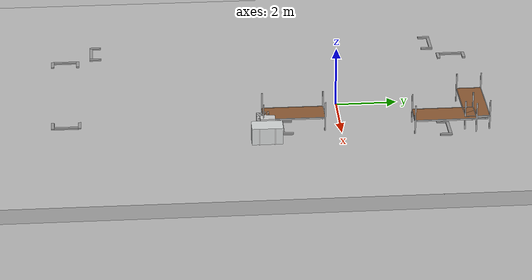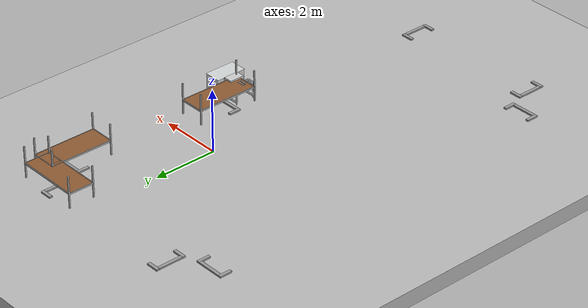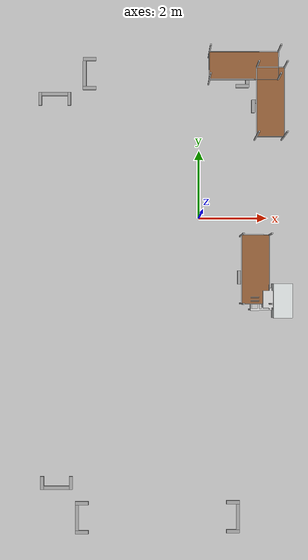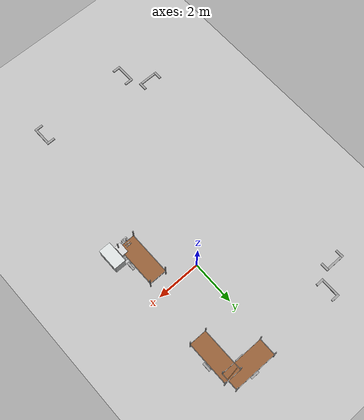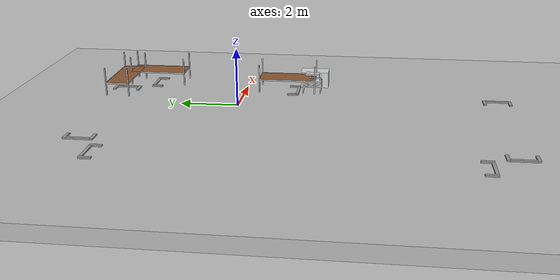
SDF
<sdf version="1.6">
 <world name="default">
  <light name="light0" type="directional">
   <pose>0 -18.818 8 0.75 -0 0</pose>
   <diffuse>0.5 0.5 0.5 1</diffuse>
   <specular>0.1 0.1 0.1 1</specular>
   <direction>0.1 0.1 -0.9</direction>
   <attenuation>
    <range>20</range>
    <constant>0.5</constant>
    <linear>0.01</linear>
    <quadratic>0.001</quadratic>
   </attenuation>
   <cast_shadows>0</cast_shadows>
  </light>
  <light name="light3" type="directional">
   <pose>3.9239 1.64974 4 0 1.2 0</pose>
   <diffuse>0.5 0.5 0.5 1</diffuse>
   <specular>0.1 0.1 0.1 1</specular>
   <direction>0.1 0.1 -0.9</direction>
   <attenuation>
    <range>20</range>
    <constant>0.5</constant>
    <linear>0.01</linear>
    <quadratic>0.001</quadratic>
   </attenuation>
   <cast_shadows>0</cast_shadows>
  </light>
  <light name="light5" type="directional">
   <pose>0.454419 12.4783 5 -0.8 0 0</pose>
   <diffuse>0.5 0.5 0.5 1</diffuse>
   <specular>0.1 0.1 0.1 1</specular>
   <direction>0.1 0.1 -0.9</direction>
   <attenuation>
    <range>20</range>
    <constant>0.5</constant>
    <linear>0.01</linear>
    <quadratic>0.001</quadratic>
   </attenuation>
   <cast_shadows>0</cast_shadows>
  </light>
  <scene>
   <shadows>false</shadows>
   <ambient>0.5 0.5 0.5 1.0</ambient>
   <grid>false</grid>
   <sky><time>22</time><sunrise>20</sunrise><sunset>21</sunset><clouds><humidity>0</humidity></clouds></sky>
  </scene>
  <include><uri>model://ground_plane</uri></include>
  <include><uri>model://moon_surface</uri><pose>0 0 -0.25 0 0 0</pose></include>
  <include><uri>model://rack_base</uri><name>rack_base</name><pose>1.421 4.35 0.05 0 -0 -1.57</pose></include>
  <include><uri>model://rack</uri><name>rack1</name><pose>1.26 4.35 0.1 0 -0 3.14</pose></include>
  <include><uri>model://rack</uri><name>rack2</name><pose>2.03 3.30 0.1 0 -0 -1.57</pose></include>
  <include><uri>model://rack</uri><name>rack3</name><pose>1.6 -1.54 0.1 0 -0 1.57</pose></include>
  <include><uri>model://arm_base</uri><name>arm_base</name><pose>1.78 -2.4 0.253 0 -0 0.0</pose></include>
  <include><uri>model://drop_table</uri><name>table</name><pose>2.4 -2.45 0 0 -0 0.0</pose></include>
  <plugin name="gazebo_link_attacher" filename="libgazebo_link_attacher.so"/>
  <plugin name="gazebo_link_ur5_attacher" filename="libgazebo_link_ur5_attacher.so"/>
 </world>
</sdf>

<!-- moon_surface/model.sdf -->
<sdf version="1.6">
  <model name="moon_surface">
    <static>true</static>

    <link name="link">
      <pose>0 0 0.003 0 0 0</pose>

      <visual name="visual1">
        <cast_shadows>false</cast_shadows>
        <geometry>
          <mesh><uri>model://moon_surface/meshes/moon_surface.dae</uri></mesh>
        </geometry>
        <material>
          <shader type='pixel'/>
        </material>
        <pose>0 0 0 0 0 0</pose>
        <transparency>0</transparency>
      </visual>
    </link>
  </model>
</sdf>

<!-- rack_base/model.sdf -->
<sdf version='1.7'>
  <model name='rack_base'>
    <link name='link'>
      <inertial>
        <pose>0 0 0 0 -0.0 0.0</pose>
        <mass>1.87</mass>
        <inertia>
          <ixx>0.01857</ixx>
          <ixy>0</ixy>
          <ixz>0</ixz>
          <iyy>0.015598</iyy>
          <iyz>0</iyz>
          <izz>0.00305</izz>
        </inertia>
      </inertial>
      <self_collide>0</self_collide>
      <enable_wind>0</enable_wind>
      <kinematic>0</kinematic>
      <pose>0 -0.154224 0 0 -0 0</pose>
      <gravity>1</gravity>
      <visual name='visual_3'>
        <cast_shadows>0</cast_shadows>
        <geometry>
          <box>
            <size>0.1 0.39 0.05</size>
          </box>
        </geometry>
        <material>
          <lighting>1</lighting>
          <script>
            <uri>file://media/materials/scripts/gazebo.material</uri>
            <name>Gazebo/Grey</name>
          </script>
          <shader type='pixel'>
            <normal_map>__default__</normal_map>
          </shader>
          <ambient>0.3 0.3 0.3 1</ambient>
          <diffuse>0.7 0.7 0.7 1</diffuse>
          <specular>0.01 0.01 0.01 1</specular>
          <emissive>0 0 0 1</emissive>
        </material>
        <pose>0.43 0.01 0 0 -0 0</pose>
        <transparency>0</transparency>
      </visual>
      <visual name='visual_4'>
        <cast_shadows>0</cast_shadows>
        <geometry>
          <box>
            <size>0.1 0.39 0.05</size>
          </box>
        </geometry>
        <material>
          <lighting>1</lighting>
          <script>
            <uri>file://media/materials/scripts/gazebo.material</uri>
            <name>Gazebo/Grey</name>
          </script>
          <shader type='pixel'>
            <normal_map>__default__</normal_map>
          </shader>
          <ambient>0.3 0.3 0.3 1</ambient>
          <diffuse>0.7 0.7 0.7 1</diffuse>
          <specular>0.01 0.01 0.01 1</specular>
          <emissive>0 0 0 1</emissive>
        </material>
        <pose>-0.43 0.01 0 0 -0 0</pose>
        <transparency>0</transparency>
      </visual>
      <visual name='visual_1'>
        <cast_shadows>0</cast_shadows>
        <geometry>
          <box>
            <size>0.76 0.1 0.05</size>
          </box>
        </geometry>
        <material>
          <lighting>1</lighting>
          <script>
            <uri>file://media/materials/scripts/gazebo.material</uri>
            <name>Gazebo/Grey</name>
          </script>
          <shader type='pixel'>
            <normal_map>__default__</normal_map>
          </shader>
          <ambient>0.3 0.3 0.3 1</ambient>
          <diffuse>0.7 0.7 0.7 1</diffuse>
          <specular>0.01 0.01 0.01 1</specular>
          <emissive>0 0 0 1</emissive>
        </material>
        <pose>0 0.155 0 0 -0 0</pose>
        <transparency>0</transparency>
      </visual>
      <collision name='collision_7'>
        <laser_retro>0</laser_retro>
        <max_contacts>10</max_contacts>
        <pose>0.43 0.01 0 0 -0 0</pose>
        <geometry>
          <box>
            <size>0.1 0.39 0.05</size>
          </box>
        </geometry>
        <surface>
          <friction>
            <ode>
              <mu>1</mu>
              <mu2>1</mu2>
              <fdir1>0 0 0</fdir1>
              <slip1>0</slip1>
              <slip2>0</slip2>
            </ode>
            <torsional>
              <coefficient>1</coefficient>
              <patch_radius>0</patch_radius>
              <surface_radius>0</surface_radius>
              <use_patch_radius>1</use_patch_radius>
              <ode>
                <slip>0</slip>
              </ode>
            </torsional>
          </friction>
          <bounce>
            <restitution_coefficient>0</restitution_coefficient>
            <threshold>1e+06</threshold>
          </bounce>
          <contact>
            <collide_without_contact>0</collide_without_contact>
            <collide_without_contact_bitmask>1</collide_without_contact_bitmask>
            <collide_bitmask>1</collide_bitmask>
            <ode>
              <soft_cfm>0</soft_cfm>
              <soft_erp>0.2</soft_erp>
              <kp>1e+13</kp>
              <kd>1</kd>
              <max_vel>0.01</max_vel>
              <min_depth>0</min_depth>
            </ode>
            <bullet>
              <split_impulse>1</split_impulse>
              <split_impulse_penetration_threshold>-0.01</split_impulse_penetration_threshold>
              <soft_cfm>0</soft_cfm>
              <soft_erp>0.2</soft_erp>
              <kp>1e+13</kp>
              <kd>1</kd>
            </bullet>
          </contact>
        </surface>
      </collision>
      <collision name='collision_8'>
        <laser_retro>0</laser_retro>
        <max_contacts>10</max_contacts>
        <pose>-0.43 0.01 0 0 -0 0</pose>
        <geometry>
          <box>
            <size>0.1 0.39 0.05</size>
          </box>
        </geometry>
        <surface>
          <friction>
            <ode>
              <mu>1</mu>
              <mu2>1</mu2>
              <fdir1>0 0 0</fdir1>
              <slip1>0</slip1>
              <slip2>0</slip2>
            </ode>
            <torsional>
              <coefficient>1</coefficient>
              <patch_radius>0</patch_radius>
              <surface_radius>0</surface_radius>
              <use_patch_radius>1</use_patch_radius>
              <ode>
                <slip>0</slip>
              </ode>
            </torsional>
          </friction>
          <bounce>
            <restitution_coefficient>0</restitution_coefficient>
            <threshold>1e+06</threshold>
          </bounce>
          <contact>
            <collide_without_contact>0</collide_without_contact>
            <collide_without_contact_bitmask>1</collide_without_contact_bitmask>
            <collide_bitmask>1</collide_bitmask>
            <ode>
              <soft_cfm>0</soft_cfm>
              <soft_erp>0.2</soft_erp>
              <kp>1e+13</kp>
              <kd>1</kd>
              <max_vel>0.01</max_vel>
              <min_depth>0</min_depth>
            </ode>
            <bullet>
              <split_impulse>1</split_impulse>
              <split_impulse_penetration_threshold>-0.01</split_impulse_penetration_threshold>
              <soft_cfm>0</soft_cfm>
              <soft_erp>0.2</soft_erp>
              <kp>1e+13</kp>
              <kd>1</kd>
            </bullet>
          </contact>
        </surface>
      </collision>
      <collision name='collision_6'>
        <laser_retro>0</laser_retro>
        <max_contacts>10</max_contacts>
        <pose>0 0.155 0 0 -0 0</pose>
        <geometry>
          <box>
            <size>0.76 0.1 0.05</size>
          </box>
        </geometry>
        <surface>
          <friction>
            <ode>
              <mu>1</mu>
              <mu2>1</mu2>
              <fdir1>0 0 0</fdir1>
              <slip1>0</slip1>
              <slip2>0</slip2>
            </ode>
            <torsional>
              <coefficient>1</coefficient>
              <patch_radius>0</patch_radius>
              <surface_radius>0</surface_radius>
              <use_patch_radius>1</use_patch_radius>
              <ode>
                <slip>0</slip>
              </ode>
            </torsional>
          </friction>
          <bounce>
            <restitution_coefficient>0</restitution_coefficient>
            <threshold>1e+06</threshold>
          </bounce>
          <contact>
            <collide_without_contact>0</collide_without_contact>
            <collide_without_contact_bitmask>1</collide_without_contact_bitmask>
            <collide_bitmask>1</collide_bitmask>
            <ode>
              <soft_cfm>0</soft_cfm>
              <soft_erp>0.2</soft_erp>
              <kp>1e+13</kp>
              <kd>1</kd>
              <max_vel>0.01</max_vel>
              <min_depth>0</min_depth>
            </ode>
            <bullet>
              <split_impulse>1</split_impulse>
              <split_impulse_penetration_threshold>-0.01</split_impulse_penetration_threshold>
              <soft_cfm>0</soft_cfm>
              <soft_erp>0.2</soft_erp>
              <kp>1e+13</kp>
              <kd>1</kd>
            </bullet>
          </contact>
        </surface>
      </collision>
    </link>
    <link name='link_clone'>
      <inertial>
        <pose>0 0 0 0 -0 0</pose>
        <mass>1.87</mass>
        <inertia>
          <ixx>0.01857</ixx>
          <ixy>0</ixy>
          <ixz>0</ixz>
          <iyy>0.015598</iyy>
          <iyz>0</iyz>
          <izz>0.00305</izz>
        </inertia>
      </inertial>
      <self_collide>0</self_collide>
      <enable_wind>0</enable_wind>
      <kinematic>0</kinematic>
      <pose>1.04088 0.608999 0 0 -0 1.57</pose>
      <gravity>1</gravity>
      <visual name='visual_1'>
        <cast_shadows>0</cast_shadows>
        <geometry>
          <box>
            <size>0.76 0.1 0.05</size>
          </box>
        </geometry>
        <material>
          <lighting>1</lighting>
          <script>
            <uri>file://media/materials/scripts/gazebo.material</uri>
            <name>Gazebo/Grey</name>
          </script>
          <shader type='pixel'>
            <normal_map>__default__</normal_map>
          </shader>
          <ambient>0.3 0.3 0.3 1</ambient>
          <diffuse>0.7 0.7 0.7 1</diffuse>
          <specular>0.01 0.01 0.01 1</specular>
          <emissive>0 0 0 1</emissive>
        </material>
        <pose>0 0.155 0 0 -0 0</pose>
        <transparency>0</transparency>
      </visual>
      <visual name='visual_3'>
        <cast_shadows>0</cast_shadows>
        <geometry>
          <box>
            <size>0.1 0.39 0.05</size>
          </box>
        </geometry>
        <material>
          <lighting>1</lighting>
          <script>
            <uri>file://media/materials/scripts/gazebo.material</uri>
            <name>Gazebo/Grey</name>
          </script>
          <shader type='pixel'>
            <normal_map>__default__</normal_map>
          </shader>
          <ambient>0.3 0.3 0.3 1</ambient>
          <diffuse>0.7 0.7 0.7 1</diffuse>
          <specular>0.01 0.01 0.01 1</specular>
          <emissive>0 0 0 1</emissive>
        </material>
        <pose>0.43 0.01 0 0 -0 0</pose>
        <transparency>0</transparency>
      </visual>
      <visual name='visual_4'>
        <cast_shadows>0</cast_shadows>
        <geometry>
          <box>
            <size>0.1 0.39 0.05</size>
          </box>
        </geometry>
        <material>
          <lighting>1</lighting>
          <script>
            <uri>file://media/materials/scripts/gazebo.material</uri>
            <name>Gazebo/Grey</name>
          </script>
          <shader type='pixel'>
            <normal_map>__default__</normal_map>
          </shader>
          <ambient>0.3 0.3 0.3 1</ambient>
          <diffuse>0.7 0.7 0.7 1</diffuse>
          <specular>0.01 0.01 0.01 1</specular>
          <emissive>0 0 0 1</emissive>
        </material>
        <pose>-0.43 0.01 0 0 -0 0</pose>
        <transparency>0</transparency>
      </visual>
      <collision name='collision_7'>
        <laser_retro>0</laser_retro>
        <max_contacts>10</max_contacts>
        <pose>0.43 0.01 0 0 -0 0</pose>
        <geometry>
          <box>
            <size>0.1 0.39 0.05</size>
          </box>
        </geometry>
        <surface>
          <friction>
            <ode>
              <mu>1</mu>
              <mu2>1</mu2>
              <fdir1>0 0 0</fdir1>
              <slip1>0</slip1>
              <slip2>0</slip2>
            </ode>
            <torsional>
              <coefficient>1</coefficient>
              <patch_radius>0</patch_radius>
              <surface_radius>0</surface_radius>
              <use_patch_radius>1</use_patch_radius>
              <ode>
                <slip>0</slip>
              </ode>
            </torsional>
          </friction>
          <bounce>
            <restitution_coefficient>0</restitution_coefficient>
            <threshold>1e+06</threshold>
          </bounce>
          <contact>
            <collide_without_contact>0</collide_without_contact>
            <collide_without_contact_bitmask>1</collide_without_contact_bitmask>
            <collide_bitmask>1</collide_bitmask>
            <ode>
              <soft_cfm>0</soft_cfm>
              <soft_erp>0.2</soft_erp>
              <kp>1e+13</kp>
              <kd>1</kd>
              <max_vel>0.01</max_vel>
              <min_depth>0</min_depth>
            </ode>
            <bullet>
              <split_impulse>1</split_impulse>
              <split_impulse_penetration_threshold>-0.01</split_impulse_penetration_threshold>
              <soft_cfm>0</soft_cfm>
              <soft_erp>0.2</soft_erp>
              <kp>1e+13</kp>
              <kd>1</kd>
            </bullet>
          </contact>
        </surface>
      </collision>
      <collision name='collision_8'>
        <laser_retro>0</laser_retro>
        <max_contacts>10</max_contacts>
        <pose>-0.43 0.01 0 0 -0 0</pose>
        <geometry>
          <box>
            <size>0.1 0.39 0.05</size>
          </box>
        </geometry>
        <surface>
          <friction>
            <ode>
              <mu>1</mu>
              <mu2>1</mu2>
              <fdir1>0 0 0</fdir1>
              <slip1>0</slip1>
              <slip2>0</slip2>
            </ode>
            <torsional>
              <coefficient>1</coefficient>
              <patch_radius>0</patch_radius>
              <surface_radius>0</surface_radius>
              <use_patch_radius>1</use_patch_radius>
              <ode>
                <slip>0</slip>
              </ode>
            </torsional>
          </friction>
          <bounce>
            <restitution_coefficient>0</restitution_coefficient>
            <threshold>1e+06</threshold>
          </bounce>
          <contact>
            <collide_without_contact>0</collide_without_contact>
            <collide_without_contact_bitmask>1</collide_without_contact_bitmask>
            <collide_bitmask>1</collide_bitmask>
            <ode>
              <soft_cfm>0</soft_cfm>
              <soft_erp>0.2</soft_erp>
              <kp>1e+13</kp>
              <kd>1</kd>
              <max_vel>0.01</max_vel>
              <min_depth>0</min_depth>
            </ode>
            <bullet>
              <split_impulse>1</split_impulse>
              <split_impulse_penetration_threshold>-0.01</split_impulse_penetration_threshold>
              <soft_cfm>0</soft_cfm>
              <soft_erp>0.2</soft_erp>
              <kp>1e+13</kp>
              <kd>1</kd>
            </bullet>
          </contact>
        </surface>
      </collision>
      <collision name='collision_6'>
        <laser_retro>0</laser_retro>
        <max_contacts>10</max_contacts>
        <pose>0 0.155 0 0 -0 0</pose>
        <geometry>
          <box>
            <size>0.76 0.1 0.05</size>
          </box>
        </geometry>
        <surface>
          <friction>
            <ode>
              <mu>1</mu>
              <mu2>1</mu2>
              <fdir1>0 0 0</fdir1>
              <slip1>0</slip1>
              <slip2>0</slip2>
            </ode>
            <torsional>
              <coefficient>1</coefficient>
              <patch_radius>0</patch_radius>
              <surface_radius>0</surface_radius>
              <use_patch_radius>1</use_patch_radius>
              <ode>
                <slip>0</slip>
              </ode>
            </torsional>
          </friction>
          <bounce>
            <restitution_coefficient>0</restitution_coefficient>
            <threshold>1e+06</threshold>
          </bounce>
          <contact>
            <collide_without_contact>0</collide_without_contact>
            <collide_without_contact_bitmask>1</collide_without_contact_bitmask>
            <collide_bitmask>1</collide_bitmask>
            <ode>
              <soft_cfm>0</soft_cfm>
              <soft_erp>0.2</soft_erp>
              <kp>1e+13</kp>
              <kd>1</kd>
              <max_vel>0.01</max_vel>
              <min_depth>0</min_depth>
            </ode>
            <bullet>
              <split_impulse>1</split_impulse>
              <split_impulse_penetration_threshold>-0.01</split_impulse_penetration_threshold>
              <soft_cfm>0</soft_cfm>
              <soft_erp>0.2</soft_erp>
              <kp>1e+13</kp>
              <kd>1</kd>
            </bullet>
          </contact>
        </surface>
      </collision>
    </link>
    <link name='link_clone_clone'>
      <inertial>
        <pose>0 0 0 0 -0 0</pose>
        <mass>1.87</mass>
        <inertia>
          <ixx>0.01857</ixx>
          <ixy>0</ixy>
          <ixz>0</ixz>
          <iyy>0.015598</iyy>
          <iyz>0</iyz>
          <izz>0.00305</izz>
        </inertia>
      </inertial>
      <self_collide>0</self_collide>
      <enable_wind>0</enable_wind>
      <kinematic>0</kinematic>
      <pose>0.063792 -4.66838 0 0 -0 3.14</pose>
      <gravity>1</gravity>
      <visual name='visual_3'>
        <cast_shadows>0</cast_shadows>
        <geometry>
          <box>
            <size>0.1 0.39 0.05</size>
          </box>
        </geometry>
        <material>
          <lighting>1</lighting>
          <script>
            <uri>file://media/materials/scripts/gazebo.material</uri>
            <name>Gazebo/Grey</name>
          </script>
          <shader type='pixel'>
            <normal_map>__default__</normal_map>
          </shader>
          <ambient>0.3 0.3 0.3 1</ambient>
          <diffuse>0.7 0.7 0.7 1</diffuse>
          <specular>0.01 0.01 0.01 1</specular>
          <emissive>0 0 0 1</emissive>
        </material>
        <pose>0.43 0.01 0 0 -0 0</pose>
        <transparency>0</transparency>
      </visual>
      <visual name='visual_1'>
        <cast_shadows>0</cast_shadows>
        <geometry>
          <box>
            <size>0.76 0.1 0.05</size>
          </box>
        </geometry>
        <material>
          <lighting>1</lighting>
          <script>
            <uri>file://media/materials/scripts/gazebo.material</uri>
            <name>Gazebo/Grey</name>
          </script>
          <shader type='pixel'>
            <normal_map>__default__</normal_map>
          </shader>
          <ambient>0.3 0.3 0.3 1</ambient>
          <diffuse>0.7 0.7 0.7 1</diffuse>
          <specular>0.01 0.01 0.01 1</specular>
          <emissive>0 0 0 1</emissive>
        </material>
        <pose>0 0.155 0 0 -0 0</pose>
        <transparency>0</transparency>
      </visual>
      <visual name='visual_4'>
        <cast_shadows>0</cast_shadows>
        <geometry>
          <box>
            <size>0.1 0.39 0.05</size>
          </box>
        </geometry>
        <material>
          <lighting>1</lighting>
          <script>
            <uri>file://media/materials/scripts/gazebo.material</uri>
            <name>Gazebo/Grey</name>
          </script>
          <shader type='pixel'>
            <normal_map>__default__</normal_map>
          </shader>
          <ambient>0.3 0.3 0.3 1</ambient>
          <diffuse>0.7 0.7 0.7 1</diffuse>
          <specular>0.01 0.01 0.01 1</specular>
          <emissive>0 0 0 1</emissive>
        </material>
        <pose>-0.43 0.01 0 0 -0 0</pose>
        <transparency>0</transparency>
      </visual>
      <collision name='collision_8'>
        <laser_retro>0</laser_retro>
        <max_contacts>10</max_contacts>
        <pose>-0.43 0.01 0 0 -0 0</pose>
        <geometry>
          <box>
            <size>0.1 0.39 0.05</size>
          </box>
        </geometry>
        <surface>
          <friction>
            <ode>
              <mu>1</mu>
              <mu2>1</mu2>
              <fdir1>0 0 0</fdir1>
              <slip1>0</slip1>
              <slip2>0</slip2>
            </ode>
            <torsional>
              <coefficient>1</coefficient>
              <patch_radius>0</patch_radius>
              <surface_radius>0</surface_radius>
              <use_patch_radius>1</use_patch_radius>
              <ode>
                <slip>0</slip>
              </ode>
            </torsional>
          </friction>
          <bounce>
            <restitution_coefficient>0</restitution_coefficient>
            <threshold>1e+06</threshold>
          </bounce>
          <contact>
            <collide_without_contact>0</collide_without_contact>
            <collide_without_contact_bitmask>1</collide_without_contact_bitmask>
            <collide_bitmask>1</collide_bitmask>
            <ode>
              <soft_cfm>0</soft_cfm>
              <soft_erp>0.2</soft_erp>
              <kp>1e+13</kp>
              <kd>1</kd>
              <max_vel>0.01</max_vel>
              <min_depth>0</min_depth>
            </ode>
            <bullet>
              <split_impulse>1</split_impulse>
              <split_impulse_penetration_threshold>-0.01</split_impulse_penetration_threshold>
              <soft_cfm>0</soft_cfm>
              <soft_erp>0.2</soft_erp>
              <kp>1e+13</kp>
              <kd>1</kd>
            </bullet>
          </contact>
        </surface>
      </collision>
      <collision name='collision_7'>
        <laser_retro>0</laser_retro>
        <max_contacts>10</max_contacts>
        <pose>0.43 0.01 0 0 -0 0</pose>
        <geometry>
          <box>
            <size>0.1 0.39 0.05</size>
          </box>
        </geometry>
        <surface>
          <friction>
            <ode>
              <mu>1</mu>
              <mu2>1</mu2>
              <fdir1>0 0 0</fdir1>
              <slip1>0</slip1>
              <slip2>0</slip2>
            </ode>
            <torsional>
              <coefficient>1</coefficient>
              <patch_radius>0</patch_radius>
              <surface_radius>0</surface_radius>
              <use_patch_radius>1</use_patch_radius>
              <ode>
                <slip>0</slip>
              </ode>
            </torsional>
          </friction>
          <bounce>
            <restitution_coefficient>0</restitution_coefficient>
            <threshold>1e+06</threshold>
          </bounce>
          <contact>
            <collide_without_contact>0</collide_without_contact>
            <collide_without_contact_bitmask>1</collide_without_contact_bitmask>
            <collide_bitmask>1</collide_bitmask>
            <ode>
              <soft_cfm>0</soft_cfm>
              <soft_erp>0.2</soft_erp>
              <kp>1e+13</kp>
              <kd>1</kd>
              <max_vel>0.01</max_vel>
              <min_depth>0</min_depth>
            </ode>
            <bullet>
              <split_impulse>1</split_impulse>
              <split_impulse_penetration_threshold>-0.01</split_impulse_penetration_threshold>
              <soft_cfm>0</soft_cfm>
              <soft_erp>0.2</soft_erp>
              <kp>1e+13</kp>
              <kd>1</kd>
            </bullet>
          </contact>
        </surface>
      </collision>
      <collision name='collision_6'>
        <laser_retro>0</laser_retro>
        <max_contacts>10</max_contacts>
        <pose>0 0.155 0 0 -0 0</pose>
        <geometry>
          <box>
            <size>0.76 0.1 0.05</size>
          </box>
        </geometry>
        <surface>
          <friction>
            <ode>
              <mu>1</mu>
              <mu2>1</mu2>
              <fdir1>0 0 0</fdir1>
              <slip1>0</slip1>
              <slip2>0</slip2>
            </ode>
            <torsional>
              <coefficient>1</coefficient>
              <patch_radius>0</patch_radius>
              <surface_radius>0</surface_radius>
              <use_patch_radius>1</use_patch_radius>
              <ode>
                <slip>0</slip>
              </ode>
            </torsional>
          </friction>
          <bounce>
            <restitution_coefficient>0</restitution_coefficient>
            <threshold>1e+06</threshold>
          </bounce>
          <contact>
            <collide_without_contact>0</collide_without_contact>
            <collide_without_contact_bitmask>1</collide_without_contact_bitmask>
            <collide_bitmask>1</collide_bitmask>
            <ode>
              <soft_cfm>0</soft_cfm>
              <soft_erp>0.2</soft_erp>
              <kp>1e+13</kp>
              <kd>1</kd>
              <max_vel>0.01</max_vel>
              <min_depth>0</min_depth>
            </ode>
            <bullet>
              <split_impulse>1</split_impulse>
              <split_impulse_penetration_threshold>-0.01</split_impulse_penetration_threshold>
              <soft_cfm>0</soft_cfm>
              <soft_erp>0.2</soft_erp>
              <kp>1e+13</kp>
              <kd>1</kd>
            </bullet>
          </contact>
        </surface>
      </collision>
    </link>
    <link name='link_clone_clone_0'>
      <inertial>
        <pose>0 0 0 0 -0 0</pose>
        <mass>1.87</mass>
        <inertia>
          <ixx>0.01857</ixx>
          <ixy>0</ixy>
          <ixz>0</ixz>
          <iyy>0.015598</iyy>
          <iyz>0</iyz>
          <izz>0.00305</izz>
        </inertia>
      </inertial>
      <self_collide>0</self_collide>
      <enable_wind>0</enable_wind>
      <kinematic>0</kinematic>
      <pose>0.823684 -5.70923 0 0 -0 1.57</pose>
      <gravity>1</gravity>
      <visual name='visual_1'>
        <cast_shadows>0</cast_shadows>
        <geometry>
          <box>
            <size>0.76 0.1 0.05</size>
          </box>
        </geometry>
        <material>
          <lighting>1</lighting>
          <script>
            <uri>file://media/materials/scripts/gazebo.material</uri>
            <name>Gazebo/Grey</name>
          </script>
          <shader type='pixel'>
            <normal_map>__default__</normal_map>
          </shader>
          <ambient>0.3 0.3 0.3 1</ambient>
          <diffuse>0.7 0.7 0.7 1</diffuse>
          <specular>0.01 0.01 0.01 1</specular>
          <emissive>0 0 0 1</emissive>
        </material>
        <pose>0 0.155 0 0 -0 0</pose>
        <transparency>0</transparency>
      </visual>
      <visual name='visual_4'>
        <cast_shadows>0</cast_shadows>
        <geometry>
          <box>
            <size>0.1 0.39 0.05</size>
          </box>
        </geometry>
        <material>
          <lighting>1</lighting>
          <script>
            <uri>file://media/materials/scripts/gazebo.material</uri>
            <name>Gazebo/Grey</name>
          </script>
          <shader type='pixel'>
            <normal_map>__default__</normal_map>
          </shader>
          <ambient>0.3 0.3 0.3 1</ambient>
          <diffuse>0.7 0.7 0.7 1</diffuse>
          <specular>0.01 0.01 0.01 1</specular>
          <emissive>0 0 0 1</emissive>
        </material>
        <pose>-0.43 0.01 0 0 -0 0</pose>
        <transparency>0</transparency>
      </visual>
      <visual name='visual_3'>
        <cast_shadows>0</cast_shadows>
        <geometry>
          <box>
            <size>0.1 0.39 0.05</size>
          </box>
        </geometry>
        <material>
          <lighting>1</lighting>
          <script>
            <uri>file://media/materials/scripts/gazebo.material</uri>
            <name>Gazebo/Grey</name>
          </script>
          <shader type='pixel'>
            <normal_map>__default__</normal_map>
          </shader>
          <ambient>0.3 0.3 0.3 1</ambient>
          <diffuse>0.7 0.7 0.7 1</diffuse>
          <specular>0.01 0.01 0.01 1</specular>
          <emissive>0 0 0 1</emissive>
        </material>
        <pose>0.43 0.01 0 0 -0 0</pose>
        <transparency>0</transparency>
      </visual>
      <collision name='collision_8'>
        <laser_retro>0</laser_retro>
        <max_contacts>10</max_contacts>
        <pose>-0.43 0.01 0 0 -0 0</pose>
        <geometry>
          <box>
            <size>0.1 0.39 0.05</size>
          </box>
        </geometry>
        <surface>
          <friction>
            <ode>
              <mu>1</mu>
              <mu2>1</mu2>
              <fdir1>0 0 0</fdir1>
              <slip1>0</slip1>
              <slip2>0</slip2>
            </ode>
            <torsional>
              <coefficient>1</coefficient>
              <patch_radius>0</patch_radius>
              <surface_radius>0</surface_radius>
              <use_patch_radius>1</use_patch_radius>
              <ode>
                <slip>0</slip>
              </ode>
            </torsional>
          </friction>
          <bounce>
            <restitution_coefficient>0</restitution_coefficient>
            <threshold>1e+06</threshold>
          </bounce>
          <contact>
            <collide_without_contact>0</collide_without_contact>
            <collide_without_contact_bitmask>1</collide_without_contact_bitmask>
            <collide_bitmask>1</collide_bitmask>
            <ode>
              <soft_cfm>0</soft_cfm>
              <soft_erp>0.2</soft_erp>
              <kp>1e+13</kp>
              <kd>1</kd>
              <max_vel>0.01</max_vel>
              <min_depth>0</min_depth>
            </ode>
            <bullet>
              <split_impulse>1</split_impulse>
              <split_impulse_penetration_threshold>-0.01</split_impulse_penetration_threshold>
              <soft_cfm>0</soft_cfm>
              <soft_erp>0.2</soft_erp>
              <kp>1e+13</kp>
              <kd>1</kd>
            </bullet>
          </contact>
        </surface>
      </collision>
      <collision name='collision_6'>
        <laser_retro>0</laser_retro>
        <max_contacts>10</max_contacts>
        <pose>0 0.155 0 0 -0 0</pose>
        <geometry>
          <box>
            <size>0.76 0.1 0.05</size>
          </box>
        </geometry>
        <surface>
          <friction>
            <ode>
              <mu>1</mu>
              <mu2>1</mu2>
              <fdir1>0 0 0</fdir1>
              <slip1>0</slip1>
              <slip2>0</slip2>
            </ode>
            <torsional>
              <coefficient>1</coefficient>
              <patch_radius>0</patch_radius>
              <surface_radius>0</surface_radius>
              <use_patch_radius>1</use_patch_radius>
              <ode>
                <slip>0</slip>
              </ode>
            </torsional>
          </friction>
          <bounce>
            <restitution_coefficient>0</restitution_coefficient>
            <threshold>1e+06</threshold>
          </bounce>
          <contact>
            <collide_without_contact>0</collide_without_contact>
            <collide_without_contact_bitmask>1</collide_without_contact_bitmask>
            <collide_bitmask>1</collide_bitmask>
            <ode>
              <soft_cfm>0</soft_cfm>
              <soft_erp>0.2</soft_erp>
              <kp>1e+13</kp>
              <kd>1</kd>
              <max_vel>0.01</max_vel>
              <min_depth>0</min_depth>
            </ode>
            <bullet>
              <split_impulse>1</split_impulse>
              <split_impulse_penetration_threshold>-0.01</split_impulse_penetration_threshold>
              <soft_cfm>0</soft_cfm>
              <soft_erp>0.2</soft_erp>
              <kp>1e+13</kp>
              <kd>1</kd>
            </bullet>
          </contact>
        </surface>
      </collision>
      <collision name='collision_7'>
        <laser_retro>0</laser_retro>
        <max_contacts>10</max_contacts>
        <pose>0.43 0.01 0 0 -0 0</pose>
        <geometry>
          <box>
            <size>0.1 0.39 0.05</size>
          </box>
        </geometry>
        <surface>
          <friction>
            <ode>
              <mu>1</mu>
              <mu2>1</mu2>
              <fdir1>0 0 0</fdir1>
              <slip1>0</slip1>
              <slip2>0</slip2>
            </ode>
            <torsional>
              <coefficient>1</coefficient>
              <patch_radius>0</patch_radius>
              <surface_radius>0</surface_radius>
              <use_patch_radius>1</use_patch_radius>
              <ode>
                <slip>0</slip>
              </ode>
            </torsional>
          </friction>
          <bounce>
            <restitution_coefficient>0</restitution_coefficient>
            <threshold>1e+06</threshold>
          </bounce>
          <contact>
            <collide_without_contact>0</collide_without_contact>
            <collide_without_contact_bitmask>1</collide_without_contact_bitmask>
            <collide_bitmask>1</collide_bitmask>
            <ode>
              <soft_cfm>0</soft_cfm>
              <soft_erp>0.2</soft_erp>
              <kp>1e+13</kp>
              <kd>1</kd>
              <max_vel>0.01</max_vel>
              <min_depth>0</min_depth>
            </ode>
            <bullet>
              <split_impulse>1</split_impulse>
              <split_impulse_penetration_threshold>-0.01</split_impulse_penetration_threshold>
              <soft_cfm>0</soft_cfm>
              <soft_erp>0.2</soft_erp>
              <kp>1e+13</kp>
              <kd>1</kd>
            </bullet>
          </contact>
        </surface>
      </collision>
    </link>
    <link name='link_clone_clone_1'>
      <inertial>
        <pose>0 0 0 0 -0 0</pose>
        <mass>1.87</mass>
        <inertia>
          <ixx>0.01857</ixx>
          <ixy>0</ixy>
          <ixz>0</ixz>
          <iyy>0.015598</iyy>
          <iyz>0</iyz>
          <izz>0.00305</izz>
        </inertia>
      </inertial>
      <self_collide>0</self_collide>
      <enable_wind>0</enable_wind>
      <kinematic>0</kinematic>
      <pose>13.2129 -0.430131 0 0 -0 0</pose>
      <gravity>1</gravity>
      <visual name='visual_1'>
        <cast_shadows>0</cast_shadows>
        <geometry>
          <box>
            <size>0.76 0.1 0.05</size>
          </box>
        </geometry>
        <material>
          <lighting>1</lighting>
          <script>
            <uri>file://media/materials/scripts/gazebo.material</uri>
            <name>Gazebo/Grey</name>
          </script>
          <shader type='pixel'>
            <normal_map>__default__</normal_map>
          </shader>
          <ambient>0.3 0.3 0.3 1</ambient>
          <diffuse>0.7 0.7 0.7 1</diffuse>
          <specular>0.01 0.01 0.01 1</specular>
          <emissive>0 0 0 1</emissive>
        </material>
        <pose>0 0.155 0 0 -0 0</pose>
        <transparency>0</transparency>
      </visual>
      <visual name='visual_3'>
        <cast_shadows>0</cast_shadows>
        <geometry>
          <box>
            <size>0.1 0.39 0.05</size>
          </box>
        </geometry>
        <material>
          <lighting>1</lighting>
          <script>
            <uri>file://media/materials/scripts/gazebo.material</uri>
            <name>Gazebo/Grey</name>
          </script>
          <shader type='pixel'>
            <normal_map>__default__</normal_map>
          </shader>
          <ambient>0.3 0.3 0.3 1</ambient>
          <diffuse>0.7 0.7 0.7 1</diffuse>
          <specular>0.01 0.01 0.01 1</specular>
          <emissive>0 0 0 1</emissive>
        </material>
        <pose>0.43 0.01 0 0 -0 0</pose>
        <transparency>0</transparency>
      </visual>
      <visual name='visual_4'>
        <cast_shadows>0</cast_shadows>
        <geometry>
          <box>
            <size>0.1 0.39 0.05</size>
          </box>
        </geometry>
        <material>
          <lighting>1</lighting>
          <script>
            <uri>file://media/materials/scripts/gazebo.material</uri>
            <name>Gazebo/Grey</name>
          </script>
          <shader type='pixel'>
            <normal_map>__default__</normal_map>
          </shader>
          <ambient>0.3 0.3 0.3 1</ambient>
          <diffuse>0.7 0.7 0.7 1</diffuse>
          <specular>0.01 0.01 0.01 1</specular>
          <emissive>0 0 0 1</emissive>
        </material>
        <pose>-0.43 0.01 0 0 -0 0</pose>
        <transparency>0</transparency>
      </visual>
      <collision name='collision_7'>
        <laser_retro>0</laser_retro>
        <max_contacts>10</max_contacts>
        <pose>0.43 0.01 0 0 -0 0</pose>
        <geometry>
          <box>
            <size>0.1 0.39 0.05</size>
          </box>
        </geometry>
        <surface>
          <friction>
            <ode>
              <mu>1</mu>
              <mu2>1</mu2>
              <fdir1>0 0 0</fdir1>
              <slip1>0</slip1>
              <slip2>0</slip2>
            </ode>
            <torsional>
              <coefficient>1</coefficient>
              <patch_radius>0</patch_radius>
              <surface_radius>0</surface_radius>
              <use_patch_radius>1</use_patch_radius>
              <ode>
                <slip>0</slip>
              </ode>
            </torsional>
          </friction>
          <bounce>
            <restitution_coefficient>0</restitution_coefficient>
            <threshold>1e+06</threshold>
          </bounce>
          <contact>
            <collide_without_contact>0</collide_without_contact>
            <collide_without_contact_bitmask>1</collide_without_contact_bitmask>
            <collide_bitmask>1</collide_bitmask>
            <ode>
              <soft_cfm>0</soft_cfm>
              <soft_erp>0.2</soft_erp>
              <kp>1e+13</kp>
              <kd>1</kd>
              <max_vel>0.01</max_vel>
              <min_depth>0</min_depth>
            </ode>
            <bullet>
              <split_impulse>1</split_impulse>
              <split_impulse_penetration_threshold>-0.01</split_impulse_penetration_threshold>
              <soft_cfm>0</soft_cfm>
              <soft_erp>0.2</soft_erp>
              <kp>1e+13</kp>
              <kd>1</kd>
            </bullet>
          </contact>
        </surface>
      </collision>
      <collision name='collision_8'>
        <laser_retro>0</laser_retro>
        <max_contacts>10</max_contacts>
        <pose>-0.43 0.01 0 0 -0 0</pose>
        <geometry>
          <box>
            <size>0.1 0.39 0.05</size>
          </box>
        </geometry>
        <surface>
          <friction>
            <ode>
              <mu>1</mu>
              <mu2>1</mu2>
              <fdir1>0 0 0</fdir1>
              <slip1>0</slip1>
              <slip2>0</slip2>
            </ode>
            <torsional>
              <coefficient>1</coefficient>
              <patch_radius>0</patch_radius>
              <surface_radius>0</surface_radius>
              <use_patch_radius>1</use_patch_radius>
              <ode>
                <slip>0</slip>
              </ode>
            </torsional>
          </friction>
          <bounce>
            <restitution_coefficient>0</restitution_coefficient>
            <threshold>1e+06</threshold>
          </bounce>
          <contact>
            <collide_without_contact>0</collide_without_contact>
            <collide_without_contact_bitmask>1</collide_without_contact_bitmask>
            <collide_bitmask>1</collide_bitmask>
            <ode>
              <soft_cfm>0</soft_cfm>
              <soft_erp>0.2</soft_erp>
              <kp>1e+13</kp>
              <kd>1</kd>
              <max_vel>0.01</max_vel>
              <min_depth>0</min_depth>
            </ode>
            <bullet>
              <split_impulse>1</split_impulse>
              <split_impulse_penetration_threshold>-0.01</split_impulse_penetration_threshold>
              <soft_cfm>0</soft_cfm>
              <soft_erp>0.2</soft_erp>
              <kp>1e+13</kp>
              <kd>1</kd>
            </bullet>
          </contact>
        </surface>
      </collision>
      <collision name='collision_6'>
        <laser_retro>0</laser_retro>
        <max_contacts>10</max_contacts>
        <pose>0 0.155 0 0 -0 0</pose>
        <geometry>
          <box>
            <size>0.76 0.1 0.05</size>
          </box>
        </geometry>
        <surface>
          <friction>
            <ode>
              <mu>1</mu>
              <mu2>1</mu2>
              <fdir1>0 0 0</fdir1>
              <slip1>0</slip1>
              <slip2>0</slip2>
            </ode>
            <torsional>
              <coefficient>1</coefficient>
              <patch_radius>0</patch_radius>
              <surface_radius>0</surface_radius>
              <use_patch_radius>1</use_patch_radius>
              <ode>
                <slip>0</slip>
              </ode>
            </torsional>
          </friction>
          <bounce>
            <restitution_coefficient>0</restitution_coefficient>
            <threshold>1e+06</threshold>
          </bounce>
          <contact>
            <collide_without_contact>0</collide_without_contact>
            <collide_without_contact_bitmask>1</collide_without_contact_bitmask>
            <collide_bitmask>1</collide_bitmask>
            <ode>
              <soft_cfm>0</soft_cfm>
              <soft_erp>0.2</soft_erp>
              <kp>1e+13</kp>
              <kd>1</kd>
              <max_vel>0.01</max_vel>
              <min_depth>0</min_depth>
            </ode>
            <bullet>
              <split_impulse>1</split_impulse>
              <split_impulse_penetration_threshold>-0.01</split_impulse_penetration_threshold>
              <soft_cfm>0</soft_cfm>
              <soft_erp>0.2</soft_erp>
              <kp>1e+13</kp>
              <kd>1</kd>
            </bullet>
          </contact>
        </surface>
      </collision>
    </link>
    <link name='link_clone_clone_2'>
      <inertial>
        <pose>0 0 0 0 -0 0</pose>
        <mass>1.87</mass>
        <inertia>
          <ixx>2.02</ixx>
          <ixy>-8.09</ixy>
          <ixz>1.57</ixz>
          <iyy>0.015598</iyy>
          <iyz>0</iyz>
          <izz>0.00305</izz>
        </inertia>
      </inertial>
      <self_collide>0</self_collide>
      <enable_wind>0</enable_wind>
      <kinematic>0</kinematic>
      <pose>6.100000 0.190000 0 -0 0 4.71</pose>
      <gravity>1</gravity>
      <visual name='visual_1'>
        <cast_shadows>0</cast_shadows>
        <geometry>
          <box>
            <size>0.76 0.1 0.05</size>
          </box>
        </geometry>
        <material>
          <lighting>1</lighting>
          <script>
            <uri>file://media/materials/scripts/gazebo.material</uri>
            <name>Gazebo/Grey</name>
          </script>
          <shader type='pixel'>
            <normal_map>__default__</normal_map>
          </shader>
          <ambient>0.3 0.3 0.3 1</ambient>
          <diffuse>0.7 0.7 0.7 1</diffuse>
          <specular>0.01 0.01 0.01 1</specular>
          <emissive>0 0 0 1</emissive>
        </material>
        <pose>0 0.155 0 0 -0 0</pose>
        <transparency>0</transparency>
      </visual>
      <visual name='visual_3'>
        <cast_shadows>0</cast_shadows>
        <geometry>
          <box>
            <size>0.1 0.39 0.05</size>
          </box>
        </geometry>
        <material>
          <lighting>1</lighting>
          <script>
            <uri>file://media/materials/scripts/gazebo.material</uri>
            <name>Gazebo/Grey</name>
          </script>
          <shader type='pixel'>
            <normal_map>__default__</normal_map>
          </shader>
          <ambient>0.3 0.3 0.3 1</ambient>
          <diffuse>0.7 0.7 0.7 1</diffuse>
          <specular>0.01 0.01 0.01 1</specular>
          <emissive>0 0 0 1</emissive>
        </material>
        <pose>0.43 0.01 0 0 -0 0</pose>
        <transparency>0</transparency>
      </visual>
      <visual name='visual_4'>
        <cast_shadows>0</cast_shadows>
        <geometry>
          <box>
            <size>0.1 0.39 0.05</size>
          </box>
        </geometry>
        <material>
          <lighting>1</lighting>
          <script>
            <uri>file://media/materials/scripts/gazebo.material</uri>
            <name>Gazebo/Grey</name>
          </script>
          <shader type='pixel'>
            <normal_map>__default__</normal_map>
          </shader>
          <ambient>0.3 0.3 0.3 1</ambient>
          <diffuse>0.7 0.7 0.7 1</diffuse>
          <specular>0.01 0.01 0.01 1</specular>
          <emissive>0 0 0 1</emissive>
        </material>
        <pose>-0.43 0.01 0 0 -0 0</pose>
        <transparency>0</transparency>
      </visual>
      <collision name='collision_7'>
        <laser_retro>0</laser_retro>
        <max_contacts>10</max_contacts>
        <pose>0.43 0.01 0 0 -0 0</pose>
        <geometry>
          <box>
            <size>0.1 0.39 0.05</size>
          </box>
        </geometry>
        <surface>
          <friction>
            <ode>
              <mu>1</mu>
              <mu2>1</mu2>
              <fdir1>0 0 0</fdir1>
              <slip1>0</slip1>
              <slip2>0</slip2>
            </ode>
            <torsional>
              <coefficient>1</coefficient>
              <patch_radius>0</patch_radius>
              <surface_radius>0</surface_radius>
              <use_patch_radius>1</use_patch_radius>
              <ode>
                <slip>0</slip>
              </ode>
            </torsional>
          </friction>
          <bounce>
            <restitution_coefficient>0</restitution_coefficient>
            <threshold>1e+06</threshold>
          </bounce>
          <contact>
            <collide_without_contact>0</collide_without_contact>
            <collide_without_contact_bitmask>1</collide_without_contact_bitmask>
            <collide_bitmask>1</collide_bitmask>
            <ode>
              <soft_cfm>0</soft_cfm>
              <soft_erp>0.2</soft_erp>
              <kp>1e+13</kp>
              <kd>1</kd>
              <max_vel>0.01</max_vel>
              <min_depth>0</min_depth>
            </ode>
            <bullet>
              <split_impulse>1</split_impulse>
              <split_impulse_penetration_threshold>-0.01</split_impulse_penetration_threshold>
              <soft_cfm>0</soft_cfm>
              <soft_erp>0.2</soft_erp>
              <kp>1e+13</kp>
              <kd>1</kd>
            </bullet>
          </contact>
        </surface>
      </collision>
      <collision name='collision_8'>
        <laser_retro>0</laser_retro>
        <max_contacts>10</max_contacts>
        <pose>-0.43 0.01 0 0 -0 0</pose>
        <geometry>
          <box>
            <size>0.1 0.39 0.05</size>
          </box>
        </geometry>
        <surface>
          <friction>
            <ode>
              <mu>1</mu>
              <mu2>1</mu2>
              <fdir1>0 0 0</fdir1>
              <slip1>0</slip1>
              <slip2>0</slip2>
            </ode>
            <torsional>
              <coefficient>1</coefficient>
              <patch_radius>0</patch_radius>
              <surface_radius>0</surface_radius>
              <use_patch_radius>1</use_patch_radius>
              <ode>
                <slip>0</slip>
              </ode>
            </torsional>
          </friction>
          <bounce>
            <restitution_coefficient>0</restitution_coefficient>
            <threshold>1e+06</threshold>
          </bounce>
          <contact>
            <collide_without_contact>0</collide_without_contact>
            <collide_without_contact_bitmask>1</collide_without_contact_bitmask>
            <collide_bitmask>1</collide_bitmask>
            <ode>
              <soft_cfm>0</soft_cfm>
              <soft_erp>0.2</soft_erp>
              <kp>1e+13</kp>
              <kd>1</kd>
              <max_vel>0.01</max_vel>
              <min_depth>0</min_depth>
            </ode>
            <bullet>
              <split_impulse>1</split_impulse>
              <split_impulse_penetration_threshold>-0.01</split_impulse_penetration_threshold>
              <soft_cfm>0</soft_cfm>
              <soft_erp>0.2</soft_erp>
              <kp>1e+13</kp>
              <kd>1</kd>
            </bullet>
          </contact>
        </surface>
      </collision>
      <collision name='collision_6'>
        <laser_retro>0</laser_retro>
        <max_contacts>10</max_contacts>
        <pose>0 0.155 0 0 -0 0</pose>
        <geometry>
          <box>
            <size>0.76 0.1 0.05</size>
          </box>
        </geometry>
        <surface>
          <friction>
            <ode>
              <mu>1</mu>
              <mu2>1</mu2>
              <fdir1>0 0 0</fdir1>
              <slip1>0</slip1>
              <slip2>0</slip2>
            </ode>
            <torsional>
              <coefficient>1</coefficient>
              <patch_radius>0</patch_radius>
              <surface_radius>0</surface_radius>
              <use_patch_radius>1</use_patch_radius>
              <ode>
                <slip>0</slip>
              </ode>
            </torsional>
          </friction>
          <bounce>
            <restitution_coefficient>0</restitution_coefficient>
            <threshold>1e+06</threshold>
          </bounce>
          <contact>
            <collide_without_contact>0</collide_without_contact>
            <collide_without_contact_bitmask>1</collide_without_contact_bitmask>
            <collide_bitmask>1</collide_bitmask>
            <ode>
              <soft_cfm>0</soft_cfm>
              <soft_erp>0.2</soft_erp>
              <kp>1e+13</kp>
              <kd>1</kd>
              <max_vel>0.01</max_vel>
              <min_depth>0</min_depth>
            </ode>
            <bullet>
              <split_impulse>1</split_impulse>
              <split_impulse_penetration_threshold>-0.01</split_impulse_penetration_threshold>
              <soft_cfm>0</soft_cfm>
              <soft_erp>0.2</soft_erp>
              <kp>1e+13</kp>
              <kd>1</kd>
            </bullet>
          </contact>
        </surface>
      </collision>
    </link>
    <link name='link_clone_clone_3'>
      <inertial>
        <pose>0 0 0 0 -0 0</pose>
        <mass>1.87</mass>
        <inertia>
          <ixx>0.01857</ixx>
          <ixy>0</ixy>
          <ixz>0</ixz>
          <iyy>0.015598</iyy>
          <iyz>0</iyz>
          <izz>0.00305</izz>
        </inertia>
      </inertial>
      <self_collide>0</self_collide>
      <enable_wind>0</enable_wind>
      <kinematic>0</kinematic>
      <pose>13.2418 -4.89365 0 0 -0 3.14</pose>
      <gravity>1</gravity>
      <visual name='visual_1'>
        <cast_shadows>0</cast_shadows>
        <geometry>
          <box>
            <size>0.76 0.1 0.05</size>
          </box>
        </geometry>
        <material>
          <lighting>1</lighting>
          <script>
            <uri>file://media/materials/scripts/gazebo.material</uri>
            <name>Gazebo/Grey</name>
          </script>
          <shader type='pixel'>
            <normal_map>__default__</normal_map>
          </shader>
          <ambient>0.3 0.3 0.3 1</ambient>
          <diffuse>0.7 0.7 0.7 1</diffuse>
          <specular>0.01 0.01 0.01 1</specular>
          <emissive>0 0 0 1</emissive>
        </material>
        <pose>0 0.155 0 0 -0 0</pose>
        <transparency>0</transparency>
      </visual>
      <visual name='visual_3'>
        <cast_shadows>0</cast_shadows>
        <geometry>
          <box>
            <size>0.1 0.39 0.05</size>
          </box>
        </geometry>
        <material>
          <lighting>1</lighting>
          <script>
            <uri>file://media/materials/scripts/gazebo.material</uri>
            <name>Gazebo/Grey</name>
          </script>
          <shader type='pixel'>
            <normal_map>__default__</normal_map>
          </shader>
          <ambient>0.3 0.3 0.3 1</ambient>
          <diffuse>0.7 0.7 0.7 1</diffuse>
          <specular>0.01 0.01 0.01 1</specular>
          <emissive>0 0 0 1</emissive>
        </material>
        <pose>0.43 0.01 0 0 -0 0</pose>
        <transparency>0</transparency>
      </visual>
      <visual name='visual_4'>
        <cast_shadows>0</cast_shadows>
        <geometry>
          <box>
            <size>0.1 0.39 0.05</size>
          </box>
        </geometry>
        <material>
          <lighting>1</lighting>
          <script>
            <uri>file://media/materials/scripts/gazebo.material</uri>
            <name>Gazebo/Grey</name>
          </script>
          <shader type='pixel'>
            <normal_map>__default__</normal_map>
          </shader>
          <ambient>0.3 0.3 0.3 1</ambient>
          <diffuse>0.7 0.7 0.7 1</diffuse>
          <specular>0.01 0.01 0.01 1</specular>
          <emissive>0 0 0 1</emissive>
        </material>
        <pose>-0.43 0.01 0 0 -0 0</pose>
        <transparency>0</transparency>
      </visual>
      <collision name='collision_7'>
        <laser_retro>0</laser_retro>
        <max_contacts>10</max_contacts>
        <pose>0.43 0.01 0 0 -0 0</pose>
        <geometry>
          <box>
            <size>0.1 0.39 0.05</size>
          </box>
        </geometry>
        <surface>
          <friction>
            <ode>
              <mu>1</mu>
              <mu2>1</mu2>
              <fdir1>0 0 0</fdir1>
              <slip1>0</slip1>
              <slip2>0</slip2>
            </ode>
            <torsional>
              <coefficient>1</coefficient>
              <patch_radius>0</patch_radius>
              <surface_radius>0</surface_radius>
              <use_patch_radius>1</use_patch_radius>
              <ode>
                <slip>0</slip>
              </ode>
            </torsional>
          </friction>
          <bounce>
            <restitution_coefficient>0</restitution_coefficient>
            <threshold>1e+06</threshold>
          </bounce>
          <contact>
            <collide_without_contact>0</collide_without_contact>
            <collide_without_contact_bitmask>1</collide_without_contact_bitmask>
            <collide_bitmask>1</collide_bitmask>
            <ode>
              <soft_cfm>0</soft_cfm>
              <soft_erp>0.2</soft_erp>
              <kp>1e+13</kp>
              <kd>1</kd>
              <max_vel>0.01</max_vel>
              <min_depth>0</min_depth>
            </ode>
            <bullet>
              <split_impulse>1</split_impulse>
              <split_impulse_penetration_threshold>-0.01</split_impulse_penetration_threshold>
              <soft_cfm>0</soft_cfm>
              <soft_erp>0.2</soft_erp>
              <kp>1e+13</kp>
              <kd>1</kd>
            </bullet>
          </contact>
        </surface>
      </collision>
      <collision name='collision_8'>
        <laser_retro>0</laser_retro>
        <max_contacts>10</max_contacts>
        <pose>-0.43 0.01 0 0 -0 0</pose>
        <geometry>
          <box>
            <size>0.1 0.39 0.05</size>
          </box>
        </geometry>
        <surface>
          <friction>
            <ode>
              <mu>1</mu>
              <mu2>1</mu2>
              <fdir1>0 0 0</fdir1>
              <slip1>0</slip1>
              <slip2>0</slip2>
            </ode>
            <torsional>
              <coefficient>1</coefficient>
              <patch_radius>0</patch_radius>
              <surface_radius>0</surface_radius>
              <use_patch_radius>1</use_patch_radius>
              <ode>
                <slip>0</slip>
              </ode>
            </torsional>
          </friction>
          <bounce>
            <restitution_coefficient>0</restitution_coefficient>
            <threshold>1e+06</threshold>
          </bounce>
          <contact>
            <collide_without_contact>0</collide_without_contact>
            <collide_without_contact_bitmask>1</collide_without_contact_bitmask>
            <collide_bitmask>1</collide_bitmask>
            <ode>
              <soft_cfm>0</soft_cfm>
              <soft_erp>0.2</soft_erp>
              <kp>1e+13</kp>
              <kd>1</kd>
              <max_vel>0.01</max_vel>
              <min_depth>0</min_depth>
            </ode>
            <bullet>
              <split_impulse>1</split_impulse>
              <split_impulse_penetration_threshold>-0.01</split_impulse_penetration_threshold>
              <soft_cfm>0</soft_cfm>
              <soft_erp>0.2</soft_erp>
              <kp>1e+13</kp>
              <kd>1</kd>
            </bullet>
          </contact>
        </surface>
      </collision>
      <collision name='collision_6'>
        <laser_retro>0</laser_retro>
        <max_contacts>10</max_contacts>
        <pose>0 0.155 0 0 -0 0</pose>
        <geometry>
          <box>
            <size>0.76 0.1 0.05</size>
          </box>
        </geometry>
        <surface>
          <friction>
            <ode>
              <mu>1</mu>
              <mu2>1</mu2>
              <fdir1>0 0 0</fdir1>
              <slip1>0</slip1>
              <slip2>0</slip2>
            </ode>
            <torsional>
              <coefficient>1</coefficient>
              <patch_radius>0</patch_radius>
              <surface_radius>0</surface_radius>
              <use_patch_radius>1</use_patch_radius>
              <ode>
                <slip>0</slip>
              </ode>
            </torsional>
          </friction>
          <bounce>
            <restitution_coefficient>0</restitution_coefficient>
            <threshold>1e+06</threshold>
          </bounce>
          <contact>
            <collide_without_contact>0</collide_without_contact>
            <collide_without_contact_bitmask>1</collide_without_contact_bitmask>
            <collide_bitmask>1</collide_bitmask>
            <ode>
              <soft_cfm>0</soft_cfm>
              <soft_erp>0.2</soft_erp>
              <kp>1e+13</kp>
              <kd>1</kd>
              <max_vel>0.01</max_vel>
              <min_depth>0</min_depth>
            </ode>
            <bullet>
              <split_impulse>1</split_impulse>
              <split_impulse_penetration_threshold>-0.01</split_impulse_penetration_threshold>
              <soft_cfm>0</soft_cfm>
              <soft_erp>0.2</soft_erp>
              <kp>1e+13</kp>
              <kd>1</kd>
            </bullet>
          </contact>
        </surface>
      </collision>
    </link>
    <link name='link_clone_clone_4'>
      <inertial>
        <pose>0 0 0 0 -0 0</pose>
        <mass>1.87</mass>
        <inertia>
          <ixx>0.01857</ixx>
          <ixy>0</ixy>
          <ixz>0</ixz>
          <iyy>0.015598</iyy>
          <iyz>0</iyz>
          <izz>0.00305</izz>
        </inertia>
      </inertial>
      <self_collide>0</self_collide>
      <enable_wind>0</enable_wind>
      <kinematic>0</kinematic>
      <pose>12.1985 -5.65606 0 0 0 -1.57</pose>
      <gravity>1</gravity>
      <visual name='visual_1'>
        <cast_shadows>0</cast_shadows>
        <geometry>
          <box>
            <size>0.76 0.1 0.05</size>
          </box>
        </geometry>
        <material>
          <lighting>1</lighting>
          <script>
            <uri>file://media/materials/scripts/gazebo.material</uri>
            <name>Gazebo/Grey</name>
          </script>
          <shader type='pixel'>
            <normal_map>__default__</normal_map>
          </shader>
          <ambient>0.3 0.3 0.3 1</ambient>
          <diffuse>0.7 0.7 0.7 1</diffuse>
          <specular>0.01 0.01 0.01 1</specular>
          <emissive>0 0 0 1</emissive>
        </material>
        <pose>0 0.155 0 0 -0 0</pose>
        <transparency>0</transparency>
      </visual>
      <visual name='visual_3'>
        <cast_shadows>0</cast_shadows>
        <geometry>
          <box>
            <size>0.1 0.39 0.05</size>
          </box>
        </geometry>
        <material>
          <lighting>1</lighting>
          <script>
            <uri>file://media/materials/scripts/gazebo.material</uri>
            <name>Gazebo/Grey</name>
          </script>
          <shader type='pixel'>
            <normal_map>__default__</normal_map>
          </shader>
          <ambient>0.3 0.3 0.3 1</ambient>
          <diffuse>0.7 0.7 0.7 1</diffuse>
          <specular>0.01 0.01 0.01 1</specular>
          <emissive>0 0 0 1</emissive>
        </material>
        <pose>0.43 0.01 0 0 -0 0</pose>
        <transparency>0</transparency>
      </visual>
      <visual name='visual_4'>
        <cast_shadows>0</cast_shadows>
        <geometry>
          <box>
            <size>0.1 0.39 0.05</size>
          </box>
        </geometry>
        <material>
          <lighting>1</lighting>
          <script>
            <uri>file://media/materials/scripts/gazebo.material</uri>
            <name>Gazebo/Grey</name>
          </script>
          <shader type='pixel'>
            <normal_map>__default__</normal_map>
          </shader>
          <ambient>0.3 0.3 0.3 1</ambient>
          <diffuse>0.7 0.7 0.7 1</diffuse>
          <specular>0.01 0.01 0.01 1</specular>
          <emissive>0 0 0 1</emissive>
        </material>
        <pose>-0.43 0.01 0 0 -0 0</pose>
        <transparency>0</transparency>
      </visual>
      <collision name='collision_7'>
        <laser_retro>0</laser_retro>
        <max_contacts>10</max_contacts>
        <pose>0.43 0.01 0 0 -0 0</pose>
        <geometry>
          <box>
            <size>0.1 0.39 0.05</size>
          </box>
        </geometry>
        <surface>
          <friction>
            <ode>
              <mu>1</mu>
              <mu2>1</mu2>
              <fdir1>0 0 0</fdir1>
              <slip1>0</slip1>
              <slip2>0</slip2>
            </ode>
            <torsional>
              <coefficient>1</coefficient>
              <patch_radius>0</patch_radius>
              <surface_radius>0</surface_radius>
              <use_patch_radius>1</use_patch_radius>
              <ode>
                <slip>0</slip>
              </ode>
            </torsional>
          </friction>
          <bounce>
            <restitution_coefficient>0</restitution_coefficient>
            <threshold>1e+06</threshold>
          </bounce>
          <contact>
            <collide_without_contact>0</collide_without_contact>
            <collide_without_contact_bitmask>1</collide_without_contact_bitmask>
            <collide_bitmask>1</collide_bitmask>
            <ode>
              <soft_cfm>0</soft_cfm>
              <soft_erp>0.2</soft_erp>
              <kp>1e+13</kp>
              <kd>1</kd>
              <max_vel>0.01</max_vel>
              <min_depth>0</min_depth>
            </ode>
            <bullet>
              <split_impulse>1</split_impulse>
              <split_impulse_penetration_threshold>-0.01</split_impulse_penetration_threshold>
              <soft_cfm>0</soft_cfm>
              <soft_erp>0.2</soft_erp>
              <kp>1e+13</kp>
              <kd>1</kd>
            </bullet>
          </contact>
        </surface>
      </collision>
      <collision name='collision_8'>
        <laser_retro>0</laser_retro>
        <max_contacts>10</max_contacts>
        <pose>-0.43 0.01 0 0 -0 0</pose>
        <geometry>
          <box>
            <size>0.1 0.39 0.05</size>
          </box>
        </geometry>
        <surface>
          <friction>
            <ode>
              <mu>1</mu>
              <mu2>1</mu2>
              <fdir1>0 0 0</fdir1>
              <slip1>0</slip1>
              <slip2>0</slip2>
            </ode>
            <torsional>
              <coefficient>1</coefficient>
              <patch_radius>0</patch_radius>
              <surface_radius>0</surface_radius>
              <use_patch_radius>1</use_patch_radius>
              <ode>
                <slip>0</slip>
              </ode>
            </torsional>
          </friction>
          <bounce>
            <restitution_coefficient>0</restitution_coefficient>
            <threshold>1e+06</threshold>
          </bounce>
          <contact>
            <collide_without_contact>0</collide_without_contact>
            <collide_without_contact_bitmask>1</collide_without_contact_bitmask>
            <collide_bitmask>1</collide_bitmask>
            <ode>
              <soft_cfm>0</soft_cfm>
              <soft_erp>0.2</soft_erp>
              <kp>1e+13</kp>
              <kd>1</kd>
              <max_vel>0.01</max_vel>
              <min_depth>0</min_depth>
            </ode>
            <bullet>
              <split_impulse>1</split_impulse>
              <split_impulse_penetration_threshold>-0.01</split_impulse_penetration_threshold>
              <soft_cfm>0</soft_cfm>
              <soft_erp>0.2</soft_erp>
              <kp>1e+13</kp>
              <kd>1</kd>
            </bullet>
          </contact>
        </surface>
      </collision>
      <collision name='collision_6'>
        <laser_retro>0</laser_retro>
        <max_contacts>10</max_contacts>
        <pose>0 0.155 0 0 -0 0</pose>
        <geometry>
          <box>
            <size>0.76 0.1 0.05</size>
          </box>
        </geometry>
        <surface>
          <friction>
            <ode>
              <mu>1</mu>
              <mu2>1</mu2>
              <fdir1>0 0 0</fdir1>
              <slip1>0</slip1>
              <slip2>0</slip2>
            </ode>
            <torsional>
              <coefficient>1</coefficient>
              <patch_radius>0</patch_radius>
              <surface_radius>0</surface_radius>
              <use_patch_radius>1</use_patch_radius>
              <ode>
                <slip>0</slip>
              </ode>
            </torsional>
          </friction>
          <bounce>
            <restitution_coefficient>0</restitution_coefficient>
            <threshold>1e+06</threshold>
          </bounce>
          <contact>
            <collide_without_contact>0</collide_without_contact>
            <collide_without_contact_bitmask>1</collide_without_contact_bitmask>
            <collide_bitmask>1</collide_bitmask>
            <ode>
              <soft_cfm>0</soft_cfm>
              <soft_erp>0.2</soft_erp>
              <kp>1e+13</kp>
              <kd>1</kd>
              <max_vel>0.01</max_vel>
              <min_depth>0</min_depth>
            </ode>
            <bullet>
              <split_impulse>1</split_impulse>
              <split_impulse_penetration_threshold>-0.01</split_impulse_penetration_threshold>
              <soft_cfm>0</soft_cfm>
              <soft_erp>0.2</soft_erp>
              <kp>1e+13</kp>
              <kd>1</kd>
            </bullet>
          </contact>
        </surface>
      </collision>
    </link>
    <static>1</static>
    <allow_auto_disable>1</allow_auto_disable>
  </model>
</sdf>

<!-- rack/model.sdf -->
<sdf version='1.6'>
  <model name='rack'>
    <link name="surface">
      <inertial>
          <mass>0.1</mass>
          <inertia>
              <ixx>0.00001</ixx>
              <ixy>0.000</ixy>
              <ixz>0.000</ixz>
              <iyy>0.00001</iyy>
              <iyz>0.000</iyz>
              <izz>0.00001</izz>
          </inertia>
      </inertial>
      <visual name='surface_visual'>
        <pose relative_to=''>0 0 0.45 0 0 0</pose>
        <geometry>
          <box>
            <size>2 0.8 0.03</size>
          </box>
        </geometry>
        <material>
          <ambient>0.55 0.35 0.2 1</ambient>
          <diffuse>0.55 0.35 0.2 1</diffuse>
          <specular>0.1 0.1 0.1 1</specular>
          <emissive>0 0 0 1</emissive>
        </material>
        <transparency>0</transparency>
        <cast_shadows>1</cast_shadows>
      </visual>
      <collision name='surface_collision'>
        <pose relative_to=''>0 0 0.45 0 0 0</pose>
        <laser_retro>0</laser_retro>
        <max_contacts>10</max_contacts>
        <geometry>
          <box>
            <size>2 0.82 0.03</size>
          </box>
        </geometry>
        <surface>
          <friction>
            <ode>
              <mu>1000000</mu>
              <mu2>1000000</mu2>
            </ode>
          </friction>
          <bounce>
            <restitution_coefficient>0</restitution_coefficient>
          </bounce>
          <contact>
            <ode>
              <kp>1e13</kp>
              <kd>1</kd>
            </ode>
          </contact>
        </surface>
      </collision>

      <visual name='left_holding_visual'>
        <pose relative_to=''>0 0.4 0.45 0 0 0</pose>
        <geometry>
          <box>
            <size>1.98 0.02 0.05</size>
          </box>
        </geometry>
        <material>
          <ambient>0.3 0.3 0.3 1</ambient>
          <diffuse>0.7 0.7 0.7 1</diffuse>
          <specular>0.01 0.01 0.01 1</specular>
          <emissive>0 0 0 1</emissive>
          <pbr>
            <metal>
              <roughness>0.8</roughness>
              <metalness>0.1</metalness>
            </metal>
          </pbr>
        </material>
        <transparency>0</transparency>
        <cast_shadows>1</cast_shadows>
      </visual>

      <visual name='right_holding_visual'>
        <pose relative_to=''>0 -0.4 0.45 0 0 0</pose>
        <geometry>
          <box>
            <size>1.98 0.02 0.05</size>
          </box>
        </geometry>
        <material>
          <ambient>0.3 0.3 0.3 1</ambient>
          <diffuse>0.7 0.7 0.7 1</diffuse>
          <specular>0.01 0.01 0.01 1</specular>
          <emissive>0 0 0 1</emissive>
          <pbr>
            <metal>
              <roughness>0.8</roughness>
              <metalness>0.1</metalness>
            </metal>
          </pbr>
        </material>
        <transparency>0</transparency>
        <cast_shadows>1</cast_shadows>
      </visual>

      <visual name='front_holding_visual'>
        <pose relative_to=''>1.0 0 0.45 0 0 1.57</pose>
        <geometry>
          <box>
            <size>0.8 0.02 0.05</size>
          </box>
        </geometry>
        <material>
          <ambient>0.3 0.3 0.3 1</ambient>
          <diffuse>0.7 0.7 0.7 1</diffuse>
          <specular>0.01 0.01 0.01 1</specular>
          <emissive>0 0 0 1</emissive>
          <pbr>
            <metal>
              <roughness>0.8</roughness>
              <metalness>0.1</metalness>
            </metal>
          </pbr>
        </material>
        <transparency>0</transparency>
        <cast_shadows>1</cast_shadows>
      </visual>

      <visual name='back_holding_visual'>
        <pose relative_to=''>-1.0 0 0.45 0 0 1.57</pose>
        <geometry>
          <box>
            <size>0.8 0.02 0.05</size>
          </box>
        </geometry>
        <material>
          <ambient>0.3 0.3 0.3 1</ambient>
          <diffuse>0.7 0.7 0.7 1</diffuse>
          <specular>0.01 0.01 0.01 1</specular>
          <emissive>0 0 0 1</emissive>
          <pbr>
            <metal>
              <roughness>0.8</roughness>
              <metalness>0.1</metalness>
            </metal>
          </pbr>
        </material>
        <transparency>0</transparency>
        <cast_shadows>1</cast_shadows>
      </visual>

      <visual name='front_left_leg_visual'>
        <pose relative_to=''>0.99 0.4 0.5 0 0 0</pose>
        <geometry>
          <box>
            <size>0.04 0.04 1.0</size>
          </box>
        </geometry>
        <material>
          <ambient>0.3 0.3 0.3 1</ambient>
          <diffuse>0.7 0.7 0.7 1</diffuse>
          <specular>0.01 0.01 0.01 1</specular>
          <emissive>0 0 0 1</emissive>
          <pbr>
            <metal>
              <roughness>0.8</roughness>
              <metalness>0.1</metalness>
            </metal>
          </pbr>
        </material>
        <cast_shadows>1</cast_shadows>
      </visual>
      <collision name='front_left_leg_collision'>
        <pose relative_to=''>0.99 0.4 0.5 0 0 0</pose>
        <laser_retro>0</laser_retro>
        <max_contacts>10</max_contacts>
        <geometry>
          <box>
            <size>0.04 0.04 1.0</size>
          </box>
        </geometry>
        <surface>
          <friction>
            <ode>
              <mu>0.1</mu>
              <mu2>0.1</mu2>
            </ode>
          </friction>
          <bounce>
            <restitution_coefficient>0</restitution_coefficient>
          </bounce>
          <contact>
            <ode>
              <kp>1e6</kp>
              <kd>1</kd>
            </ode>
          </contact>
        </surface>
      </collision>

      <visual name='front_right_leg_visual'>
        <pose relative_to=''>0.99 -0.4 0.5 0 0 0</pose>
        <geometry>
          <box>
            <size>0.04 0.04 1.0</size>
          </box>
        </geometry>
        <material>
          <ambient>0.3 0.3 0.3 1</ambient>
          <diffuse>0.7 0.7 0.7 1</diffuse>
          <specular>0.01 0.01 0.01 1</specular>
          <emissive>0 0 0 1</emissive>
          <pbr>
            <metal>
              <roughness>0.8</roughness>
              <metalness>0.1</metalness>
            </metal>
          </pbr>
        </material>
        <cast_shadows>1</cast_shadows>
      </visual>
      <collision name='front_right_leg_collision'>
        <pose relative_to=''>0.99 -0.4 0.5 0 0 0</pose>
        <laser_retro>0</laser_retro>
        <max_contacts>10</max_contacts>
        <geometry>
          <box>
            <size>0.04 0.04 1.0</size>
          </box>
        </geometry>
        <surface>
          <friction>
            <ode>
              <mu>0.1</mu>
              <mu2>0.1</mu2>
            </ode>
          </friction>
          <bounce>
            <restitution_coefficient>0</restitution_coefficient>
          </bounce>
          <contact>
            <ode>
              <kp>1e6</kp>
              <kd>1</kd>
            </ode>
          </contact>
        </surface>
      </collision>

      <visual name='back_left_leg_visual'>
        <pose relative_to=''>-0.99 0.4 0.5 0 0 0</pose>
        <geometry>
          <box>
            <size>0.04 0.04 1.0</size>
          </box>
        </geometry>
        <material>
          <ambient>0.3 0.3 0.3 1</ambient>
          <diffuse>0.7 0.7 0.7 1</diffuse>
          <specular>0.01 0.01 0.01 1</specular>
          <emissive>0 0 0 1</emissive>
          <pbr>
            <metal>
              <roughness>0.8</roughness>
              <metalness>0.1</metalness>
            </metal>
          </pbr>
        </material>
        <cast_shadows>1</cast_shadows>
      </visual>
      <collision name='back_left_leg_collision'>
        <pose relative_to=''>-0.99 0.4 0.5 0 0 0</pose>
        <laser_retro>0</laser_retro>
        <max_contacts>10</max_contacts>
        <geometry>
          <box>
            <size>0.04 0.04 1.0</size>
          </box>
        </geometry>
        <surface>
          <friction>
            <ode>
              <mu>0.1</mu>
              <mu2>0.1</mu2>
            </ode>
          </friction>
          <bounce>
            <restitution_coefficient>0</restitution_coefficient>
          </bounce>
          <contact>
            <ode>
              <kp>1e6</kp>
              <kd>1</kd>
            </ode>
          </contact>
        </surface>
      </collision>

      <visual name='back_right_leg_visual'>
        <pose relative_to=''>-0.99 -0.4 0.5 0 0 0</pose>
        <geometry>
          <box>
            <size>0.04 0.04 1.0</size>
          </box>
        </geometry>
        <material>
          <ambient>0.3 0.3 0.3 1</ambient>
          <diffuse>0.7 0.7 0.7 1</diffuse>
          <specular>0.01 0.01 0.01 1</specular>
          <emissive>0 0 0 1</emissive>
          <pbr>
            <metal>
              <roughness>0.8</roughness>
              <metalness>0.1</metalness>
            </metal>
          </pbr>
        </material>
        <cast_shadows>1</cast_shadows>
      </visual>
      <collision name='back_right_leg_collision'>
        <pose relative_to=''>-0.99 -0.4 0.5 0 0 0</pose>
        <laser_retro>0</laser_retro>
        <max_contacts>10</max_contacts>
        <geometry>
          <box>
            <size>0.04 0.04 1.0</size>
          </box>
        </geometry>
        <surface>
          <friction>
            <ode>
              <mu>0.1</mu>
              <mu2>0.1</mu2>
            </ode>
          </friction>
          <bounce>
            <restitution_coefficient>0</restitution_coefficient>
          </bounce>
          <contact>
            <ode>
              <kp>1e6</kp>
              <kd>1</kd>
            </ode>
          </contact>
        </surface>
      </collision>
    </link>

  </model>
</sdf>

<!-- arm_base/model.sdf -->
<sdf version='1.7'>
  <model name='arm_base'>
    <link name='link'>
      <inertial>
        <mass>1</mass>
        <inertia>
          <ixx>0.166667</ixx>
          <ixy>0</ixy>
          <ixz>0</ixz>
          <iyy>0.166667</iyy>
          <iyz>0</iyz>
          <izz>0.166667</izz>
        </inertia>
        <pose>0 0 0 0 -0 0</pose>
      </inertial>
      <self_collide>0</self_collide>
      <enable_wind>0</enable_wind>
      <kinematic>0</kinematic>
      <pose>0 0 0 0 -0 0</pose>
      <gravity>1</gravity>
      <visual name='visual1'>
        <cast_shadows>0</cast_shadows>
        <geometry>
          <mesh>
            <uri>model://arm_base/meshes/arm_base.dae</uri>
          </mesh>
        </geometry>
        <material>
          <shader type='pixel'>
            <normal_map>__default__</normal_map>
          </shader>
          <emissive>0 0 0 1</emissive>

        </material>
        <pose>0 0 -0.25 0 -0 0</pose>
        <transparency>0</transparency>
        <pose>0 0 0 0 -0 0</pose>
        <transparency>0</transparency>
      </visual>
      <collision name='collision'>
        <laser_retro>0</laser_retro>
        <max_contacts>10</max_contacts>
        <pose>0 0 0 0 -0 0</pose>
        <geometry>
          <box>
            <size>0.7 0.7 0.52</size>
          </box>
        </geometry>
        <surface>
          <friction>
            <ode>
              <mu>1</mu>
              <mu2>1</mu2>
              <fdir1>0 0 0</fdir1>
              <slip1>0</slip1>
              <slip2>0</slip2>
            </ode>
            <torsional>
              <coefficient>1</coefficient>
              <patch_radius>0</patch_radius>
              <surface_radius>0</surface_radius>
              <use_patch_radius>1</use_patch_radius>
              <ode>
                <slip>0</slip>
              </ode>
            </torsional>
          </friction>
          <bounce>
            <restitution_coefficient>0</restitution_coefficient>
            <threshold>1e+06</threshold>
          </bounce>
          <contact>
            <collide_without_contact>0</collide_without_contact>
            <collide_without_contact_bitmask>1</collide_without_contact_bitmask>
            <collide_bitmask>1</collide_bitmask>
            <ode>
              <soft_cfm>0</soft_cfm>
              <soft_erp>0.2</soft_erp>
              <kp>1e+13</kp>
              <kd>1</kd>
              <max_vel>0.01</max_vel>
              <min_depth>0</min_depth>
            </ode>
            <bullet>
              <split_impulse>1</split_impulse>
              <split_impulse_penetration_threshold>-0.01</split_impulse_penetration_threshold>
              <soft_cfm>0</soft_cfm>
              <soft_erp>0.2</soft_erp>
              <kp>1e+13</kp>
              <kd>1</kd>
            </bullet>
          </contact>
        </surface>
      </collision>
    </link>
    <static>1</static>
    <allow_auto_disable>1</allow_auto_disable>
  </model>
</sdf>

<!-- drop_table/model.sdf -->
<sdf version='1.7'>
  <model name='drop_table'>
    <link name='link'>
      <inertial>
        <mass>1</mass>
        <inertia>
          <ixx>0.166667</ixx>
          <ixy>0</ixy>
          <ixz>0</ixz>
          <iyy>0.166667</iyy>
          <iyz>0</iyz>
          <izz>0.166667</izz>
        </inertia>
        <pose>0 0 0 0 -0 0</pose>
      </inertial>
      <self_collide>0</self_collide>
      <enable_wind>0</enable_wind>
      <kinematic>0</kinematic>
      <pose>0 0 0 0 -0 0</pose>
      <gravity>1</gravity>
      <visual name='visual1'>
        <cast_shadows>0</cast_shadows>
        <geometry>
          <mesh>
            <uri>model://drop_table/meshes/table.dae</uri>
          </mesh>
        </geometry>
        <material>
          <shader type='pixel'>
            <normal_map>__default__</normal_map>
          </shader>
          <emissive>0 0 0 1</emissive>

        </material>
        <pose>0 0 0 0 -0 0</pose>
        <transparency>0</transparency>
        <pose>0 0 0 0 -0 0</pose>
        <transparency>0</transparency>
      </visual>
      <collision name='collision'>
        <laser_retro>0</laser_retro>
        <max_contacts>10</max_contacts>
        <pose>0 0 0.29 0 -0 0</pose>
        <geometry>
          <box>
            <size>0.5 1 0.58</size>
          </box>
        </geometry>
        <surface>
          <friction>
            <ode>
              <mu>1</mu>
              <mu2>1</mu2>
              <fdir1>0 0 0</fdir1>
              <slip1>0</slip1>
              <slip2>0</slip2>
            </ode>
            <torsional>
              <coefficient>1</coefficient>
              <patch_radius>0</patch_radius>
              <surface_radius>0</surface_radius>
              <use_patch_radius>1</use_patch_radius>
              <ode>
                <slip>0</slip>
              </ode>
            </torsional>
          </friction>
          <bounce>
            <restitution_coefficient>0</restitution_coefficient>
            <threshold>1e+06</threshold>
          </bounce>
          <contact>
            <collide_without_contact>0</collide_without_contact>
            <collide_without_contact_bitmask>1</collide_without_contact_bitmask>
            <collide_bitmask>1</collide_bitmask>
            <ode>
              <soft_cfm>0</soft_cfm>
              <soft_erp>0.2</soft_erp>
              <kp>1e+13</kp>
              <kd>1</kd>
              <max_vel>0.01</max_vel>
              <min_depth>0</min_depth>
            </ode>
            <bullet>
              <split_impulse>1</split_impulse>
              <split_impulse_penetration_threshold>-0.01</split_impulse_penetration_threshold>
              <soft_cfm>0</soft_cfm>
              <soft_erp>0.2</soft_erp>
              <kp>1e+13</kp>
              <kd>1</kd>
            </bullet>
          </contact>
        </surface>
      </collision>
    </link>
    <static>1</static>
    <allow_auto_disable>1</allow_auto_disable>
  </model>
</sdf>
